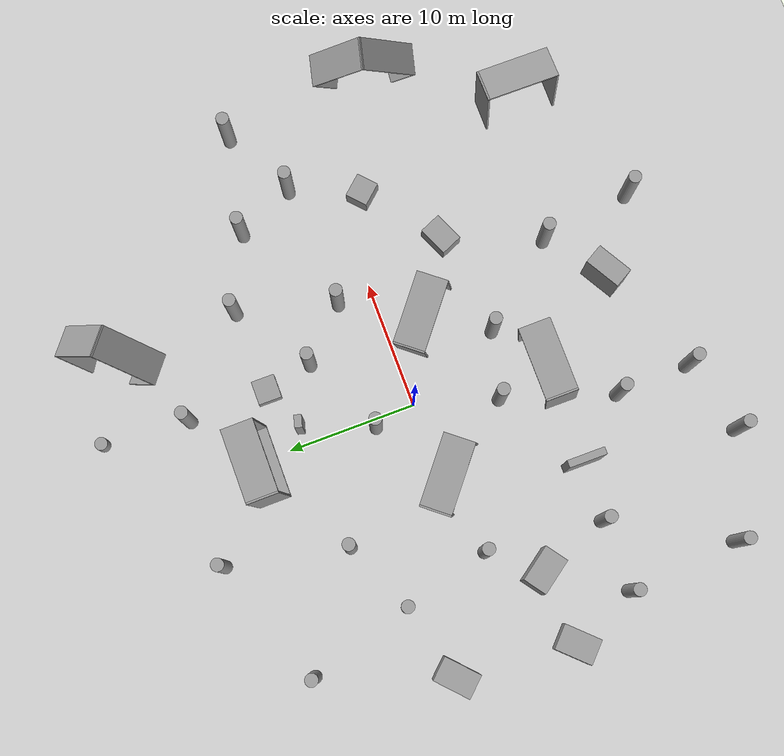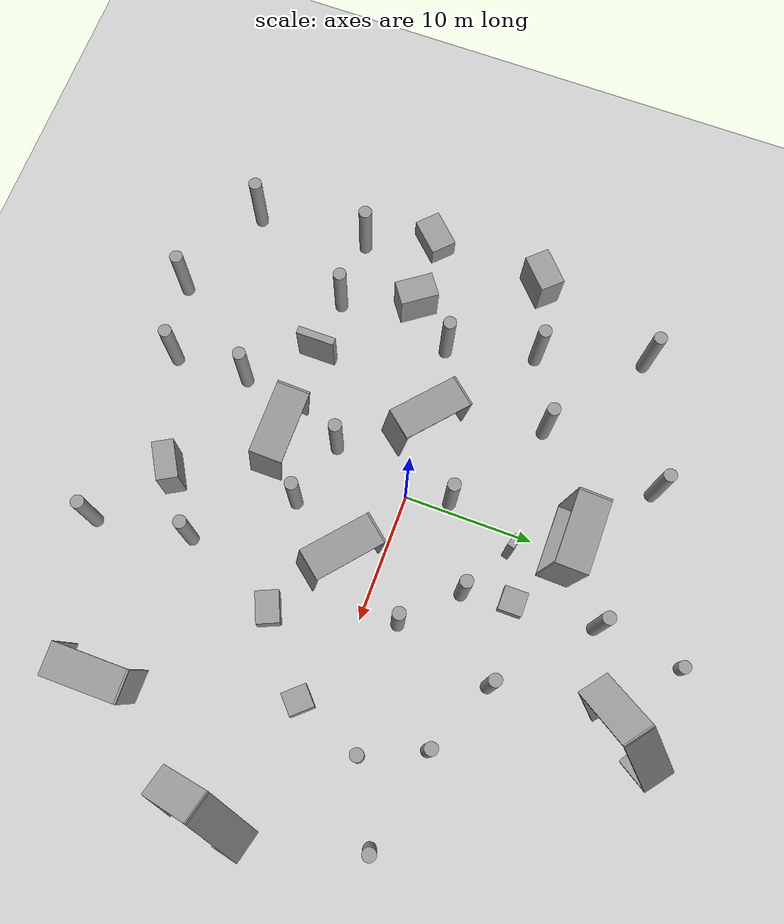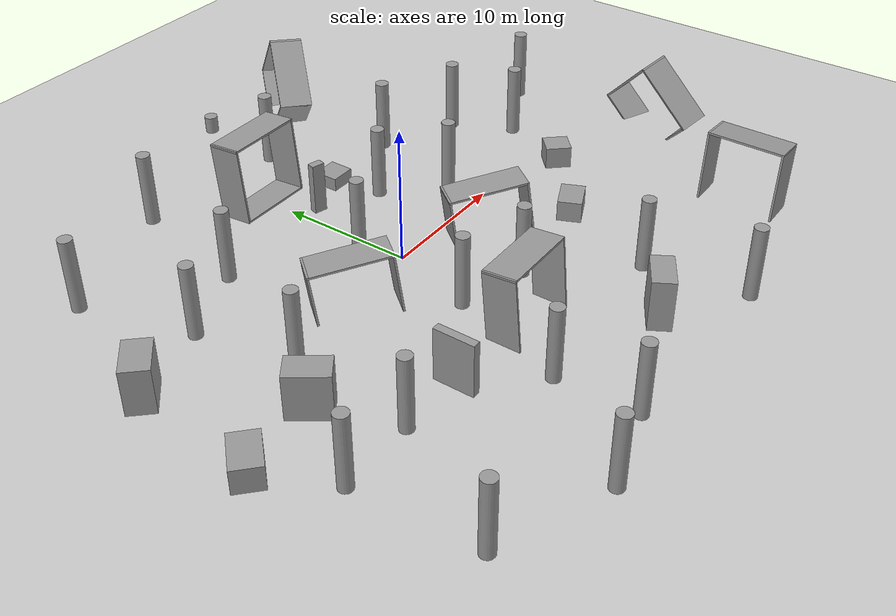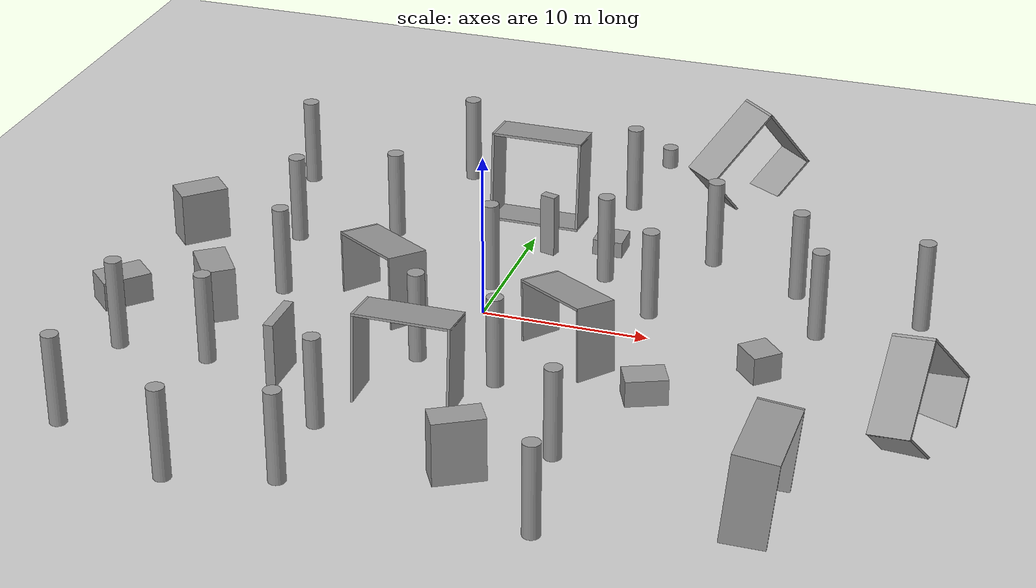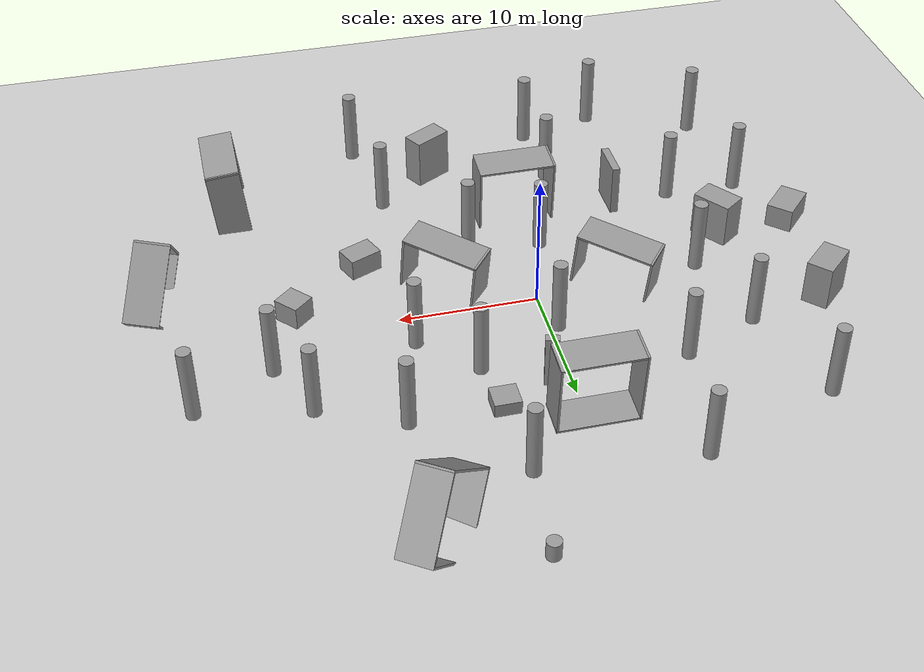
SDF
<sdf version="1.6">
 <world name="default">
  <light name="sun" type="directional">
   <pose>0 0 10 0 -0 0</pose>
   <diffuse>0.8 0.8 0.8 1</diffuse>
   <specular>0.2 0.2 0.2 1</specular>
   <attenuation>
    <range>1000</range>
    <constant>0.9</constant>
    <linear>0.01</linear>
    <quadratic>0.001</quadratic>
   </attenuation>
   <direction>-0.5 0.1 -0.9</direction>
  </light>
  <model name="ground_plane">
   <static>1</static>
   <link name="link">
    <collision name="collision">
     <geometry><plane><normal>0 0 1</normal><size>100 100</size></plane></geometry>
     <surface><friction><ode><mu>100</mu><mu2>50</mu2></ode></friction></surface>
    </collision>
    <visual name="visual">
     <cast_shadows>0</cast_shadows>
     <geometry><plane><normal>0 0 1</normal><size>100 100</size></plane></geometry>
     <material>
      <script><uri>file://media/materials/scripts/gazebo.material</uri><name>Gazebo/Grey</name></script>
     </material>
    </visual>
   </link>
  </model>
  <gravity>0 0 -9.8</gravity>
  <magnetic_field>6e-06 2.3e-05 -4.2e-05</magnetic_field>
  <atmosphere type="adiabatic"/>
  <physics name="default_physics" default="0" type="ode">
   <max_step_size>0.001</max_step_size>
   <real_time_factor>1</real_time_factor>
   <real_time_update_rate>1000</real_time_update_rate>
  </physics>
  <scene><ambient>0.4 0.4 0.4 1</ambient><background>0.7 0.7 0.7 1</background><shadows>1</shadows></scene>
  <audio><device>default</device></audio>
  <spherical_coordinates>
   <surface_model>EARTH_WGS84</surface_model>
   <latitude_deg>0</latitude_deg>
   <longitude_deg>0</longitude_deg>
   <elevation>0</elevation>
   <heading_deg>0</heading_deg>
  </spherical_coordinates>
  <model name="unit_cylinder">
   <pose>5.28034 23.1376 0.661761 0 -0 0.001729</pose>
   <link name="link">
    <inertial>
     <mass>1</mass>
     <inertia><ixx>0.145833</ixx><ixy>0</ixy><ixz>0</ixz><iyy>0.145833</iyy><iyz>0</iyz><izz>0.125</izz></inertia>
    </inertial>
    <collision name="collision">
     <geometry><cylinder><radius>0.5</radius><length>1.32353</length></cylinder></geometry>
    </collision>
    <visual name="visual">
     <geometry><cylinder><radius>0.5</radius><length>1.32353</length></cylinder></geometry>
     <material>
      <script><name>Gazebo/Grey</name><uri>file://media/materials/scripts/gazebo.material</uri></script>
     </material>
    </visual>
   </link>
  </model>
  <model name="unit_cylinder_clone_2">
   <pose>9.34612 2.72453 2.75253 0 -0 0.007033</pose>
   <link name="link">
    <inertial>
     <mass>1</mass>
     <inertia><ixx>0.145833</ixx><ixy>0</ixy><ixz>0</ixz><iyy>0.145833</iyy><iyz>0</iyz><izz>0.125</izz></inertia>
    </inertial>
    <collision name="collision">
     <geometry><cylinder><radius>0.5</radius><length>5.50507</length></cylinder></geometry>
    </collision>
    <visual name="visual">
     <geometry><cylinder><radius>0.5</radius><length>5.50507</length></cylinder></geometry>
     <material>
      <script><name>Gazebo/Grey</name><uri>file://media/materials/scripts/gazebo.material</uri></script>
     </material>
    </visual>
   </link>
  </model>
  <model name="unit_cylinder_clone_4">
   <pose>8.59201 -13.9206 2.75253 0 -0 0.007526</pose>
   <link name="link">
    <inertial>
     <mass>1</mass>
     <inertia><ixx>0.145833</ixx><ixy>0</ixy><ixz>0</ixz><iyy>0.145833</iyy><iyz>0</iyz><izz>0.125</izz></inertia>
    </inertial>
    <collision name="collision">
     <geometry><cylinder><radius>0.5</radius><length>5.50507</length></cylinder></geometry>
    </collision>
    <visual name="visual">
     <geometry><cylinder><radius>0.5</radius><length>5.50507</length></cylinder></geometry>
     <material>
      <script><name>Gazebo/Grey</name><uri>file://media/materials/scripts/gazebo.material</uri></script>
     </material>
    </visual>
   </link>
  </model>
  <model name="unit_cylinder_clone_5">
   <pose>5.63029 6.34759 2.75253 0 -0 0.006959</pose>
   <link name="link">
    <inertial>
     <mass>1</mass>
     <inertia><ixx>0.145833</ixx><ixy>0</ixy><ixz>0</ixz><iyy>0.145833</iyy><iyz>0</iyz><izz>0.125</izz></inertia>
    </inertial>
    <collision name="collision">
     <geometry><cylinder><radius>0.5</radius><length>5.50507</length></cylinder></geometry>
    </collision>
    <visual name="visual">
     <geometry><cylinder><radius>0.5</radius><length>5.50507</length></cylinder></geometry>
     <material>
      <script><name>Gazebo/Grey</name><uri>file://media/materials/scripts/gazebo.material</uri></script>
     </material>
    </visual>
   </link>
  </model>
  <model name="unit_cylinder_clone_8">
   <pose>11.3719 10.3631 2.75253 0 -0 0.007031</pose>
   <link name="link">
    <inertial>
     <mass>1</mass>
     <inertia><ixx>0.145833</ixx><ixy>0</ixy><ixz>0</ixz><iyy>0.145833</iyy><iyz>0</iyz><izz>0.125</izz></inertia>
    </inertial>
    <collision name="collision">
     <geometry><cylinder><radius>0.5</radius><length>5.50507</length></cylinder></geometry>
    </collision>
    <visual name="visual">
     <geometry><cylinder><radius>0.5</radius><length>5.50507</length></cylinder></geometry>
     <material>
      <script><name>Gazebo/Grey</name><uri>file://media/materials/scripts/gazebo.material</uri></script>
     </material>
    </visual>
   </link>
  </model>
  <model name="unit_cylinder_clone_9">
   <pose>-0.632732 3.27501 2.75253 0 -0 0.007234</pose>
   <link name="link">
    <inertial>
     <mass>1</mass>
     <inertia><ixx>0.145833</ixx><ixy>0</ixy><ixz>0</ixz><iyy>0.145833</iyy><iyz>0</iyz><izz>0.125</izz></inertia>
    </inertial>
    <collision name="collision">
     <geometry><cylinder><radius>0.5</radius><length>5.50507</length></cylinder></geometry>
    </collision>
    <visual name="visual">
     <geometry><cylinder><radius>0.5</radius><length>5.50507</length></cylinder></geometry>
     <material>
      <script><name>Gazebo/Grey</name><uri>file://media/materials/scripts/gazebo.material</uri></script>
     </material>
    </visual>
   </link>
  </model>
  <model name="unit_box_clone">
   <pose>11.597 -6.53716 0.788235 0 0 -1.1581</pose>
   <link name="link">
    <inertial>
     <mass>1</mass>
     <inertia>
      <ixx>0.166667</ixx>
      <ixy>0</ixy>
      <ixz>0</ixz>
      <iyy>0.166667</iyy>
      <iyz>0</iyz>
      <izz>0.166667</izz>
     </inertia>
    </inertial>
    <collision name="collision"><geometry><box><size>1.76997 2.44518 1.57647</size></box></geometry></collision>
    <visual name="visual">
     <geometry><box><size>1.76997 2.44518 1.57647</size></box></geometry>
     <material>
      <script><name>Gazebo/Grey</name><uri>file://media/materials/scripts/gazebo.material</uri></script>
     </material>
    </visual>
   </link>
  </model>
  <model name="unit_box_clone_0">
   <pose>17.0391 -2.04264 0.84104 0 -0 0.734782</pose>
   <link name="link">
    <inertial>
     <mass>1</mass>
     <inertia>
      <ixx>0.166667</ixx>
      <ixy>0</ixy>
      <ixz>0</ixz>
      <iyy>0.166667</iyy>
      <iyz>0</iyz>
      <izz>0.166667</izz>
     </inertia>
    </inertial>
    <collision name="collision"><geometry><box><size>1.76997 1.92154 1.68208</size></box></geometry></collision>
    <visual name="visual">
     <geometry><box><size>1.76997 1.92154 1.68208</size></box></geometry>
     <material>
      <script><name>Gazebo/Grey</name><uri>file://media/materials/scripts/gazebo.material</uri></script>
     </material>
    </visual>
   </link>
  </model>
  <model name="unit_cylinder_clone_7_clone_0">
   <pose>24.7832 6.25194 2.75253 0 -0 0.006995</pose>
   <link name="link">
    <inertial>
     <mass>1</mass>
     <inertia><ixx>0.145833</ixx><ixy>0</ixy><ixz>0</ixz><iyy>0.145833</iyy><iyz>0</iyz><izz>0.125</izz></inertia>
    </inertial>
    <collision name="collision">
     <geometry><cylinder><radius>0.5</radius><length>5.50507</length></cylinder></geometry>
    </collision>
    <visual name="visual">
     <geometry><cylinder><radius>0.5</radius><length>5.50507</length></cylinder></geometry>
     <material>
      <script><name>Gazebo/Grey</name><uri>file://media/materials/scripts/gazebo.material</uri></script>
     </material>
    </visual>
   </link>
  </model>
  <model name="unit_cylinder_clone_7_clone_2">
   <pose>-8.46768 8.17615 2.75253 0 -0 0.007287</pose>
   <link name="link">
    <inertial>
     <mass>1</mass>
     <inertia><ixx>0.145833</ixx><ixy>0</ixy><ixz>0</ixz><iyy>0.145833</iyy><iyz>0</iyz><izz>0.125</izz></inertia>
    </inertial>
    <collision name="collision">
     <geometry><cylinder><radius>0.5</radius><length>5.50507</length></cylinder></geometry>
    </collision>
    <visual name="visual">
     <geometry><cylinder><radius>0.5</radius><length>5.50507</length></cylinder></geometry>
     <material>
      <script><name>Gazebo/Grey</name><uri>file://media/materials/scripts/gazebo.material</uri></script>
     </material>
    </visual>
   </link>
  </model>
  <model name="vRoom_clone_3_clone_clone_9">
   <link name="Wall_0">
    <pose>-2.8 -0 -1e-06 -0 -0 -1.5708</pose>
    <velocity_decay><linear>0</linear><angular>0</angular></velocity_decay>
    <visual name="Wall_0_Visual">
     <pose>0 0 1.25 0 -0 0</pose>
     <geometry><box><size>5.75 0.15 2.5</size></box></geometry>
     <material>
      <script><uri>file://media/materials/scripts/gazebo.material</uri><name>Gazebo/Grey</name></script>
      <ambient>1 1 1 1</ambient>
     </material>
    </visual>
    <collision name="Wall_0_Collision">
     <pose>0 0 1.25 0 -0 0</pose>
     <geometry><box><size>5.75 0.15 2.5</size></box></geometry>
     <surface>
      <friction>
       <ode><mu>1</mu><mu2>1</mu2><fdir1>0 0 0</fdir1><slip1>0</slip1><slip2>0</slip2></ode>
       <torsional>
        <coefficient>1</coefficient>
        <patch_radius>0</patch_radius>
        <surface_radius>0</surface_radius>
        <use_patch_radius>1</use_patch_radius>
        <ode><slip>0</slip></ode>
       </torsional>
      </friction>
      <bounce><restitution_coefficient>0</restitution_coefficient><threshold>1e+06</threshold></bounce>
      <contact>
       <collide_without_contact>0</collide_without_contact>
       <collide_without_contact_bitmask>1</collide_without_contact_bitmask>
       <collide_bitmask>1</collide_bitmask>
       <ode>
        <soft_cfm>0</soft_cfm>
        <soft_erp>0.2</soft_erp>
        <kp>1e+13</kp>
        <kd>1</kd>
        <max_vel>0.01</max_vel>
        <min_depth>0</min_depth>
       </ode>
       <bullet>
        <split_impulse>1</split_impulse>
        <split_impulse_penetration_threshold>-0.01</split_impulse_penetration_threshold>
        <soft_cfm>0</soft_cfm>
        <soft_erp>0.2</soft_erp>
        <kp>1e+13</kp>
        <kd>1</kd>
       </bullet>
      </contact>
     </surface>
    </collision>
   </link>
   <link name="Wall_1">
    <pose>2e-06 -2.8 2e-06 0 -0 0</pose>
    <velocity_decay><linear>0</linear><angular>0</angular></velocity_decay>
    <visual name="Wall_1_Visual">
     <pose>0 0 1.25 0 -0 0</pose>
     <geometry><box><size>5.75 0.15 2.5</size></box></geometry>
     <material>
      <script><uri>file://media/materials/scripts/gazebo.material</uri><name>Gazebo/Grey</name></script>
      <ambient>1 1 1 1</ambient>
     </material>
    </visual>
    <collision name="Wall_1_Collision">
     <pose>0 0 1.25 0 -0 0</pose>
     <geometry><box><size>5.75 0.15 2.5</size></box></geometry>
     <surface>
      <friction>
       <ode><mu>1</mu><mu2>1</mu2><fdir1>0 0 0</fdir1><slip1>0</slip1><slip2>0</slip2></ode>
       <torsional>
        <coefficient>1</coefficient>
        <patch_radius>0</patch_radius>
        <surface_radius>0</surface_radius>
        <use_patch_radius>1</use_patch_radius>
        <ode><slip>0</slip></ode>
       </torsional>
      </friction>
      <bounce><restitution_coefficient>0</restitution_coefficient><threshold>1e+06</threshold></bounce>
      <contact>
       <collide_without_contact>0</collide_without_contact>
       <collide_without_contact_bitmask>1</collide_without_contact_bitmask>
       <collide_bitmask>1</collide_bitmask>
       <ode>
        <soft_cfm>0</soft_cfm>
        <soft_erp>0.2</soft_erp>
        <kp>1e+13</kp>
        <kd>1</kd>
        <max_vel>0.01</max_vel>
        <min_depth>0</min_depth>
       </ode>
       <bullet>
        <split_impulse>1</split_impulse>
        <split_impulse_penetration_threshold>-0.01</split_impulse_penetration_threshold>
        <soft_cfm>0</soft_cfm>
        <soft_erp>0.2</soft_erp>
        <kp>1e+13</kp>
        <kd>1</kd>
       </bullet>
      </contact>
     </surface>
    </collision>
   </link>
   <link name="Wall_2">
    <pose>2.8 0 1e-06 0 -0 1.5708</pose>
    <velocity_decay><linear>0</linear><angular>0</angular></velocity_decay>
    <visual name="Wall_2_Visual">
     <pose>0 0 1.25 0 -0 0</pose>
     <geometry><box><size>5.75 0.15 2.5</size></box></geometry>
     <material>
      <script><uri>file://media/materials/scripts/gazebo.material</uri><name>Gazebo/Grey</name></script>
      <ambient>1 1 1 1</ambient>
     </material>
    </visual>
    <collision name="Wall_2_Collision">
     <pose>0 0 1.25 0 -0 0</pose>
     <geometry><box><size>5.75 0.15 2.5</size></box></geometry>
     <surface>
      <friction>
       <ode><mu>1</mu><mu2>1</mu2><fdir1>0 0 0</fdir1><slip1>0</slip1><slip2>0</slip2></ode>
       <torsional>
        <coefficient>1</coefficient>
        <patch_radius>0</patch_radius>
        <surface_radius>0</surface_radius>
        <use_patch_radius>1</use_patch_radius>
        <ode><slip>0</slip></ode>
       </torsional>
      </friction>
      <bounce><restitution_coefficient>0</restitution_coefficient><threshold>1e+06</threshold></bounce>
      <contact>
       <collide_without_contact>0</collide_without_contact>
       <collide_without_contact_bitmask>1</collide_without_contact_bitmask>
       <collide_bitmask>1</collide_bitmask>
       <ode>
        <soft_cfm>0</soft_cfm>
        <soft_erp>0.2</soft_erp>
        <kp>1e+13</kp>
        <kd>1</kd>
        <max_vel>0.01</max_vel>
        <min_depth>0</min_depth>
       </ode>
       <bullet>
        <split_impulse>1</split_impulse>
        <split_impulse_penetration_threshold>-0.01</split_impulse_penetration_threshold>
        <soft_cfm>0</soft_cfm>
        <soft_erp>0.2</soft_erp>
        <kp>1e+13</kp>
        <kd>1</kd>
       </bullet>
      </contact>
     </surface>
    </collision>
   </link>
   <link name="Wall_3">
    <pose>-2e-06 2.8 -2e-06 0 -0 3.14159</pose>
    <velocity_decay><linear>0</linear><angular>0</angular></velocity_decay>
    <visual name="Wall_3_Visual">
     <pose>0 0 1.25 0 -0 0</pose>
     <geometry><box><size>5.75 0.15 2.5</size></box></geometry>
     <material>
      <script><uri>file://media/materials/scripts/gazebo.material</uri><name>Gazebo/Grey</name></script>
      <ambient>1 1 1 1</ambient>
     </material>
    </visual>
    <collision name="Wall_3_Collision">
     <pose>0 0 1.25 0 -0 0</pose>
     <geometry><box><size>5.75 0.15 2.5</size></box></geometry>
     <surface>
      <friction>
       <ode><mu>1</mu><mu2>1</mu2><fdir1>0 0 0</fdir1><slip1>0</slip1><slip2>0</slip2></ode>
       <torsional>
        <coefficient>1</coefficient>
        <patch_radius>0</patch_radius>
        <surface_radius>0</surface_radius>
        <use_patch_radius>1</use_patch_radius>
        <ode><slip>0</slip></ode>
       </torsional>
      </friction>
      <bounce><restitution_coefficient>0</restitution_coefficient><threshold>1e+06</threshold></bounce>
      <contact>
       <collide_without_contact>0</collide_without_contact>
       <collide_without_contact_bitmask>1</collide_without_contact_bitmask>
       <collide_bitmask>1</collide_bitmask>
       <ode>
        <soft_cfm>0</soft_cfm>
        <soft_erp>0.2</soft_erp>
        <kp>1e+13</kp>
        <kd>1</kd>
        <max_vel>0.01</max_vel>
        <min_depth>0</min_depth>
       </ode>
       <bullet>
        <split_impulse>1</split_impulse>
        <split_impulse_penetration_threshold>-0.01</split_impulse_penetration_threshold>
        <soft_cfm>0</soft_cfm>
        <soft_erp>0.2</soft_erp>
        <kp>1e+13</kp>
        <kd>1</kd>
       </bullet>
      </contact>
     </surface>
    </collision>
   </link>
   <static>1</static>
   <pose>21.486 -16.0168 2.16039 4e-06 -1.47998 -7e-06</pose>
  </model>
  <model name="vRoom_clone_3_clone_clone_9_clone_0">
   <link name="Wall_0">
    <pose>-2.8 -0 -1e-06 -0 -0 -1.5708</pose>
    <velocity_decay><linear>0</linear><angular>0</angular></velocity_decay>
    <visual name="Wall_0_Visual">
     <pose>0 0 1.25 0 -0 0</pose>
     <geometry><box><size>5.75 0.15 2.5</size></box></geometry>
     <material>
      <script><uri>file://media/materials/scripts/gazebo.material</uri><name>Gazebo/Grey</name></script>
      <ambient>1 1 1 1</ambient>
     </material>
    </visual>
    <collision name="Wall_0_Collision">
     <pose>0 0 1.25 0 -0 0</pose>
     <geometry><box><size>5.75 0.15 2.5</size></box></geometry>
     <surface>
      <friction>
       <ode><mu>1</mu><mu2>1</mu2><fdir1>0 0 0</fdir1><slip1>0</slip1><slip2>0</slip2></ode>
       <torsional>
        <coefficient>1</coefficient>
        <patch_radius>0</patch_radius>
        <surface_radius>0</surface_radius>
        <use_patch_radius>1</use_patch_radius>
        <ode><slip>0</slip></ode>
       </torsional>
      </friction>
      <bounce><restitution_coefficient>0</restitution_coefficient><threshold>1e+06</threshold></bounce>
      <contact>
       <collide_without_contact>0</collide_without_contact>
       <collide_without_contact_bitmask>1</collide_without_contact_bitmask>
       <collide_bitmask>1</collide_bitmask>
       <ode>
        <soft_cfm>0</soft_cfm>
        <soft_erp>0.2</soft_erp>
        <kp>1e+13</kp>
        <kd>1</kd>
        <max_vel>0.01</max_vel>
        <min_depth>0</min_depth>
       </ode>
       <bullet>
        <split_impulse>1</split_impulse>
        <split_impulse_penetration_threshold>-0.01</split_impulse_penetration_threshold>
        <soft_cfm>0</soft_cfm>
        <soft_erp>0.2</soft_erp>
        <kp>1e+13</kp>
        <kd>1</kd>
       </bullet>
      </contact>
     </surface>
    </collision>
   </link>
   <link name="Wall_1">
    <pose>2e-06 -2.8 2e-06 0 -0 0</pose>
    <velocity_decay><linear>0</linear><angular>0</angular></velocity_decay>
    <visual name="Wall_1_Visual">
     <pose>0 0 1.25 0 -0 0</pose>
     <geometry><box><size>5.75 0.15 2.5</size></box></geometry>
     <material>
      <script><uri>file://media/materials/scripts/gazebo.material</uri><name>Gazebo/Grey</name></script>
      <ambient>1 1 1 1</ambient>
     </material>
    </visual>
    <collision name="Wall_1_Collision">
     <pose>0 0 1.25 0 -0 0</pose>
     <geometry><box><size>5.75 0.15 2.5</size></box></geometry>
     <surface>
      <friction>
       <ode><mu>1</mu><mu2>1</mu2><fdir1>0 0 0</fdir1><slip1>0</slip1><slip2>0</slip2></ode>
       <torsional>
        <coefficient>1</coefficient>
        <patch_radius>0</patch_radius>
        <surface_radius>0</surface_radius>
        <use_patch_radius>1</use_patch_radius>
        <ode><slip>0</slip></ode>
       </torsional>
      </friction>
      <bounce><restitution_coefficient>0</restitution_coefficient><threshold>1e+06</threshold></bounce>
      <contact>
       <collide_without_contact>0</collide_without_contact>
       <collide_without_contact_bitmask>1</collide_without_contact_bitmask>
       <collide_bitmask>1</collide_bitmask>
       <ode>
        <soft_cfm>0</soft_cfm>
        <soft_erp>0.2</soft_erp>
        <kp>1e+13</kp>
        <kd>1</kd>
        <max_vel>0.01</max_vel>
        <min_depth>0</min_depth>
       </ode>
       <bullet>
        <split_impulse>1</split_impulse>
        <split_impulse_penetration_threshold>-0.01</split_impulse_penetration_threshold>
        <soft_cfm>0</soft_cfm>
        <soft_erp>0.2</soft_erp>
        <kp>1e+13</kp>
        <kd>1</kd>
       </bullet>
      </contact>
     </surface>
    </collision>
   </link>
   <link name="Wall_2">
    <pose>2.8 0 1e-06 0 -0 1.5708</pose>
    <velocity_decay><linear>0</linear><angular>0</angular></velocity_decay>
    <visual name="Wall_2_Visual">
     <pose>0 0 1.25 0 -0 0</pose>
     <geometry><box><size>5.75 0.15 2.5</size></box></geometry>
     <material>
      <script><uri>file://media/materials/scripts/gazebo.material</uri><name>Gazebo/Grey</name></script>
      <ambient>1 1 1 1</ambient>
     </material>
    </visual>
    <collision name="Wall_2_Collision">
     <pose>0 0 1.25 0 -0 0</pose>
     <geometry><box><size>5.75 0.15 2.5</size></box></geometry>
     <surface>
      <friction>
       <ode><mu>1</mu><mu2>1</mu2><fdir1>0 0 0</fdir1><slip1>0</slip1><slip2>0</slip2></ode>
       <torsional>
        <coefficient>1</coefficient>
        <patch_radius>0</patch_radius>
        <surface_radius>0</surface_radius>
        <use_patch_radius>1</use_patch_radius>
        <ode><slip>0</slip></ode>
       </torsional>
      </friction>
      <bounce><restitution_coefficient>0</restitution_coefficient><threshold>1e+06</threshold></bounce>
      <contact>
       <collide_without_contact>0</collide_without_contact>
       <collide_without_contact_bitmask>1</collide_without_contact_bitmask>
       <collide_bitmask>1</collide_bitmask>
       <ode>
        <soft_cfm>0</soft_cfm>
        <soft_erp>0.2</soft_erp>
        <kp>1e+13</kp>
        <kd>1</kd>
        <max_vel>0.01</max_vel>
        <min_depth>0</min_depth>
       </ode>
       <bullet>
        <split_impulse>1</split_impulse>
        <split_impulse_penetration_threshold>-0.01</split_impulse_penetration_threshold>
        <soft_cfm>0</soft_cfm>
        <soft_erp>0.2</soft_erp>
        <kp>1e+13</kp>
        <kd>1</kd>
       </bullet>
      </contact>
     </surface>
    </collision>
   </link>
   <link name="Wall_3">
    <pose>-2e-06 2.8 -2e-06 0 -0 3.14159</pose>
    <velocity_decay><linear>0</linear><angular>0</angular></velocity_decay>
    <visual name="Wall_3_Visual">
     <pose>0 0 1.25 0 -0 0</pose>
     <geometry><box><size>5.75 0.15 2.5</size></box></geometry>
     <material>
      <script><uri>file://media/materials/scripts/gazebo.material</uri><name>Gazebo/Grey</name></script>
      <ambient>1 1 1 1</ambient>
     </material>
    </visual>
    <collision name="Wall_3_Collision">
     <pose>0 0 1.25 0 -0 0</pose>
     <geometry><box><size>5.75 0.15 2.5</size></box></geometry>
     <surface>
      <friction>
       <ode><mu>1</mu><mu2>1</mu2><fdir1>0 0 0</fdir1><slip1>0</slip1><slip2>0</slip2></ode>
       <torsional>
        <coefficient>1</coefficient>
        <patch_radius>0</patch_radius>
        <surface_radius>0</surface_radius>
        <use_patch_radius>1</use_patch_radius>
        <ode><slip>0</slip></ode>
       </torsional>
      </friction>
      <bounce><restitution_coefficient>0</restitution_coefficient><threshold>1e+06</threshold></bounce>
      <contact>
       <collide_without_contact>0</collide_without_contact>
       <collide_without_contact_bitmask>1</collide_without_contact_bitmask>
       <collide_bitmask>1</collide_bitmask>
       <ode>
        <soft_cfm>0</soft_cfm>
        <soft_erp>0.2</soft_erp>
        <kp>1e+13</kp>
        <kd>1</kd>
        <max_vel>0.01</max_vel>
        <min_depth>0</min_depth>
       </ode>
       <bullet>
        <split_impulse>1</split_impulse>
        <split_impulse_penetration_threshold>-0.01</split_impulse_penetration_threshold>
        <soft_cfm>0</soft_cfm>
        <soft_erp>0.2</soft_erp>
        <kp>1e+13</kp>
        <kd>1</kd>
       </bullet>
      </contact>
     </surface>
    </collision>
   </link>
   <static>1</static>
   <pose>6.88312 -2.08616 1 -1.11103 -1.4406 1.99896</pose>
  </model>
  <model name="vRoom_clone_3_clone_clone_9_clone_1">
   <link name="Wall_0">
    <pose>-2.8 -0 -1e-06 -0 -0 -1.5708</pose>
    <velocity_decay><linear>0</linear><angular>0</angular></velocity_decay>
    <visual name="Wall_0_Visual">
     <pose>0 0 1.25 0 -0 0</pose>
     <geometry><box><size>5.75 0.15 2.5</size></box></geometry>
     <material>
      <script><uri>file://media/materials/scripts/gazebo.material</uri><name>Gazebo/Grey</name></script>
      <ambient>1 1 1 1</ambient>
     </material>
    </visual>
    <collision name="Wall_0_Collision">
     <pose>0 0 1.25 0 -0 0</pose>
     <geometry><box><size>5.75 0.15 2.5</size></box></geometry>
     <surface>
      <friction>
       <ode><mu>1</mu><mu2>1</mu2><fdir1>0 0 0</fdir1><slip1>0</slip1><slip2>0</slip2></ode>
       <torsional>
        <coefficient>1</coefficient>
        <patch_radius>0</patch_radius>
        <surface_radius>0</surface_radius>
        <use_patch_radius>1</use_patch_radius>
        <ode><slip>0</slip></ode>
       </torsional>
      </friction>
      <bounce><restitution_coefficient>0</restitution_coefficient><threshold>1e+06</threshold></bounce>
      <contact>
       <collide_without_contact>0</collide_without_contact>
       <collide_without_contact_bitmask>1</collide_without_contact_bitmask>
       <collide_bitmask>1</collide_bitmask>
       <ode>
        <soft_cfm>0</soft_cfm>
        <soft_erp>0.2</soft_erp>
        <kp>1e+13</kp>
        <kd>1</kd>
        <max_vel>0.01</max_vel>
        <min_depth>0</min_depth>
       </ode>
       <bullet>
        <split_impulse>1</split_impulse>
        <split_impulse_penetration_threshold>-0.01</split_impulse_penetration_threshold>
        <soft_cfm>0</soft_cfm>
        <soft_erp>0.2</soft_erp>
        <kp>1e+13</kp>
        <kd>1</kd>
       </bullet>
      </contact>
     </surface>
    </collision>
   </link>
   <link name="Wall_1">
    <pose>2e-06 -2.8 2e-06 0 -0 0</pose>
    <velocity_decay><linear>0</linear><angular>0</angular></velocity_decay>
    <visual name="Wall_1_Visual">
     <pose>0 0 1.25 0 -0 0</pose>
     <geometry><box><size>5.75 0.15 2.5</size></box></geometry>
     <material>
      <script><uri>file://media/materials/scripts/gazebo.material</uri><name>Gazebo/Grey</name></script>
      <ambient>1 1 1 1</ambient>
     </material>
    </visual>
    <collision name="Wall_1_Collision">
     <pose>0 0 1.25 0 -0 0</pose>
     <geometry><box><size>5.75 0.15 2.5</size></box></geometry>
     <surface>
      <friction>
       <ode><mu>1</mu><mu2>1</mu2><fdir1>0 0 0</fdir1><slip1>0</slip1><slip2>0</slip2></ode>
       <torsional>
        <coefficient>1</coefficient>
        <patch_radius>0</patch_radius>
        <surface_radius>0</surface_radius>
        <use_patch_radius>1</use_patch_radius>
        <ode><slip>0</slip></ode>
       </torsional>
      </friction>
      <bounce><restitution_coefficient>0</restitution_coefficient><threshold>1e+06</threshold></bounce>
      <contact>
       <collide_without_contact>0</collide_without_contact>
       <collide_without_contact_bitmask>1</collide_without_contact_bitmask>
       <collide_bitmask>1</collide_bitmask>
       <ode>
        <soft_cfm>0</soft_cfm>
        <soft_erp>0.2</soft_erp>
        <kp>1e+13</kp>
        <kd>1</kd>
        <max_vel>0.01</max_vel>
        <min_depth>0</min_depth>
       </ode>
       <bullet>
        <split_impulse>1</split_impulse>
        <split_impulse_penetration_threshold>-0.01</split_impulse_penetration_threshold>
        <soft_cfm>0</soft_cfm>
        <soft_erp>0.2</soft_erp>
        <kp>1e+13</kp>
        <kd>1</kd>
       </bullet>
      </contact>
     </surface>
    </collision>
   </link>
   <link name="Wall_2">
    <pose>2.8 0 1e-06 0 -0 1.5708</pose>
    <velocity_decay><linear>0</linear><angular>0</angular></velocity_decay>
    <visual name="Wall_2_Visual">
     <pose>0 0 1.25 0 -0 0</pose>
     <geometry><box><size>5.75 0.15 2.5</size></box></geometry>
     <material>
      <script><uri>file://media/materials/scripts/gazebo.material</uri><name>Gazebo/Grey</name></script>
      <ambient>1 1 1 1</ambient>
     </material>
    </visual>
    <collision name="Wall_2_Collision">
     <pose>0 0 1.25 0 -0 0</pose>
     <geometry><box><size>5.75 0.15 2.5</size></box></geometry>
     <surface>
      <friction>
       <ode><mu>1</mu><mu2>1</mu2><fdir1>0 0 0</fdir1><slip1>0</slip1><slip2>0</slip2></ode>
       <torsional>
        <coefficient>1</coefficient>
        <patch_radius>0</patch_radius>
        <surface_radius>0</surface_radius>
        <use_patch_radius>1</use_patch_radius>
        <ode><slip>0</slip></ode>
       </torsional>
      </friction>
      <bounce><restitution_coefficient>0</restitution_coefficient><threshold>1e+06</threshold></bounce>
      <contact>
       <collide_without_contact>0</collide_without_contact>
       <collide_without_contact_bitmask>1</collide_without_contact_bitmask>
       <collide_bitmask>1</collide_bitmask>
       <ode>
        <soft_cfm>0</soft_cfm>
        <soft_erp>0.2</soft_erp>
        <kp>1e+13</kp>
        <kd>1</kd>
        <max_vel>0.01</max_vel>
        <min_depth>0</min_depth>
       </ode>
       <bullet>
        <split_impulse>1</split_impulse>
        <split_impulse_penetration_threshold>-0.01</split_impulse_penetration_threshold>
        <soft_cfm>0</soft_cfm>
        <soft_erp>0.2</soft_erp>
        <kp>1e+13</kp>
        <kd>1</kd>
       </bullet>
      </contact>
     </surface>
    </collision>
   </link>
   <link name="Wall_3">
    <pose>-2e-06 2.8 -2e-06 0 -0 3.14159</pose>
    <velocity_decay><linear>0</linear><angular>0</angular></velocity_decay>
    <visual name="Wall_3_Visual">
     <pose>0 0 1.25 0 -0 0</pose>
     <geometry><box><size>5.75 0.15 2.5</size></box></geometry>
     <material>
      <script><uri>file://media/materials/scripts/gazebo.material</uri><name>Gazebo/Grey</name></script>
      <ambient>1 1 1 1</ambient>
     </material>
    </visual>
    <collision name="Wall_3_Collision">
     <pose>0 0 1.25 0 -0 0</pose>
     <geometry><box><size>5.75 0.15 2.5</size></box></geometry>
     <surface>
      <friction>
       <ode><mu>1</mu><mu2>1</mu2><fdir1>0 0 0</fdir1><slip1>0</slip1><slip2>0</slip2></ode>
       <torsional>
        <coefficient>1</coefficient>
        <patch_radius>0</patch_radius>
        <surface_radius>0</surface_radius>
        <use_patch_radius>1</use_patch_radius>
        <ode><slip>0</slip></ode>
       </torsional>
      </friction>
      <bounce><restitution_coefficient>0</restitution_coefficient><threshold>1e+06</threshold></bounce>
      <contact>
       <collide_without_contact>0</collide_without_contact>
       <collide_without_contact_bitmask>1</collide_without_contact_bitmask>
       <collide_bitmask>1</collide_bitmask>
       <ode>
        <soft_cfm>0</soft_cfm>
        <soft_erp>0.2</soft_erp>
        <kp>1e+13</kp>
        <kd>1</kd>
        <max_vel>0.01</max_vel>
        <min_depth>0</min_depth>
       </ode>
       <bullet>
        <split_impulse>1</split_impulse>
        <split_impulse_penetration_threshold>-0.01</split_impulse_penetration_threshold>
        <soft_cfm>0</soft_cfm>
        <soft_erp>0.2</soft_erp>
        <kp>1e+13</kp>
        <kd>1</kd>
       </bullet>
      </contact>
     </surface>
    </collision>
   </link>
   <static>1</static>
   <pose>-0.451678 13.821 3.0326 4e-06 -1.47998 1.57</pose>
  </model>
  <model name="vRoom_clone_3_clone_clone_9_clone_2">
   <link name="Wall_0">
    <pose>-2.8 -0 -1e-06 -0 -0 -1.5708</pose>
    <velocity_decay><linear>0</linear><angular>0</angular></velocity_decay>
    <visual name="Wall_0_Visual">
     <pose>0 0 1.25 0 -0 0</pose>
     <geometry><box><size>5.75 0.15 2.5</size></box></geometry>
     <material>
      <script><uri>file://media/materials/scripts/gazebo.material</uri><name>Gazebo/Grey</name></script>
      <ambient>1 1 1 1</ambient>
     </material>
    </visual>
    <collision name="Wall_0_Collision">
     <pose>0 0 1.25 0 -0 0</pose>
     <geometry><box><size>5.75 0.15 2.5</size></box></geometry>
     <surface>
      <friction>
       <ode><mu>1</mu><mu2>1</mu2><fdir1>0 0 0</fdir1><slip1>0</slip1><slip2>0</slip2></ode>
       <torsional>
        <coefficient>1</coefficient>
        <patch_radius>0</patch_radius>
        <surface_radius>0</surface_radius>
        <use_patch_radius>1</use_patch_radius>
        <ode><slip>0</slip></ode>
       </torsional>
      </friction>
      <bounce><restitution_coefficient>0</restitution_coefficient><threshold>1e+06</threshold></bounce>
      <contact>
       <collide_without_contact>0</collide_without_contact>
       <collide_without_contact_bitmask>1</collide_without_contact_bitmask>
       <collide_bitmask>1</collide_bitmask>
       <ode>
        <soft_cfm>0</soft_cfm>
        <soft_erp>0.2</soft_erp>
        <kp>1e+13</kp>
        <kd>1</kd>
        <max_vel>0.01</max_vel>
        <min_depth>0</min_depth>
       </ode>
       <bullet>
        <split_impulse>1</split_impulse>
        <split_impulse_penetration_threshold>-0.01</split_impulse_penetration_threshold>
        <soft_cfm>0</soft_cfm>
        <soft_erp>0.2</soft_erp>
        <kp>1e+13</kp>
        <kd>1</kd>
       </bullet>
      </contact>
     </surface>
    </collision>
   </link>
   <link name="Wall_1">
    <pose>2e-06 -2.8 2e-06 0 -0 0</pose>
    <velocity_decay><linear>0</linear><angular>0</angular></velocity_decay>
    <visual name="Wall_1_Visual">
     <pose>0 0 1.25 0 -0 0</pose>
     <geometry><box><size>5.75 0.15 2.5</size></box></geometry>
     <material>
      <script><uri>file://media/materials/scripts/gazebo.material</uri><name>Gazebo/Grey</name></script>
      <ambient>1 1 1 1</ambient>
     </material>
    </visual>
    <collision name="Wall_1_Collision">
     <pose>0 0 1.25 0 -0 0</pose>
     <geometry><box><size>5.75 0.15 2.5</size></box></geometry>
     <surface>
      <friction>
       <ode><mu>1</mu><mu2>1</mu2><fdir1>0 0 0</fdir1><slip1>0</slip1><slip2>0</slip2></ode>
       <torsional>
        <coefficient>1</coefficient>
        <patch_radius>0</patch_radius>
        <surface_radius>0</surface_radius>
        <use_patch_radius>1</use_patch_radius>
        <ode><slip>0</slip></ode>
       </torsional>
      </friction>
      <bounce><restitution_coefficient>0</restitution_coefficient><threshold>1e+06</threshold></bounce>
      <contact>
       <collide_without_contact>0</collide_without_contact>
       <collide_without_contact_bitmask>1</collide_without_contact_bitmask>
       <collide_bitmask>1</collide_bitmask>
       <ode>
        <soft_cfm>0</soft_cfm>
        <soft_erp>0.2</soft_erp>
        <kp>1e+13</kp>
        <kd>1</kd>
        <max_vel>0.01</max_vel>
        <min_depth>0</min_depth>
       </ode>
       <bullet>
        <split_impulse>1</split_impulse>
        <split_impulse_penetration_threshold>-0.01</split_impulse_penetration_threshold>
        <soft_cfm>0</soft_cfm>
        <soft_erp>0.2</soft_erp>
        <kp>1e+13</kp>
        <kd>1</kd>
       </bullet>
      </contact>
     </surface>
    </collision>
   </link>
   <link name="Wall_2">
    <pose>2.8 0 1e-06 0 -0 1.5708</pose>
    <velocity_decay><linear>0</linear><angular>0</angular></velocity_decay>
    <visual name="Wall_2_Visual">
     <pose>0 0 1.25 0 -0 0</pose>
     <geometry><box><size>5.75 0.15 2.5</size></box></geometry>
     <material>
      <script><uri>file://media/materials/scripts/gazebo.material</uri><name>Gazebo/Grey</name></script>
      <ambient>1 1 1 1</ambient>
     </material>
    </visual>
    <collision name="Wall_2_Collision">
     <pose>0 0 1.25 0 -0 0</pose>
     <geometry><box><size>5.75 0.15 2.5</size></box></geometry>
     <surface>
      <friction>
       <ode><mu>1</mu><mu2>1</mu2><fdir1>0 0 0</fdir1><slip1>0</slip1><slip2>0</slip2></ode>
       <torsional>
        <coefficient>1</coefficient>
        <patch_radius>0</patch_radius>
        <surface_radius>0</surface_radius>
        <use_patch_radius>1</use_patch_radius>
        <ode><slip>0</slip></ode>
       </torsional>
      </friction>
      <bounce><restitution_coefficient>0</restitution_coefficient><threshold>1e+06</threshold></bounce>
      <contact>
       <collide_without_contact>0</collide_without_contact>
       <collide_without_contact_bitmask>1</collide_without_contact_bitmask>
       <collide_bitmask>1</collide_bitmask>
       <ode>
        <soft_cfm>0</soft_cfm>
        <soft_erp>0.2</soft_erp>
        <kp>1e+13</kp>
        <kd>1</kd>
        <max_vel>0.01</max_vel>
        <min_depth>0</min_depth>
       </ode>
       <bullet>
        <split_impulse>1</split_impulse>
        <split_impulse_penetration_threshold>-0.01</split_impulse_penetration_threshold>
        <soft_cfm>0</soft_cfm>
        <soft_erp>0.2</soft_erp>
        <kp>1e+13</kp>
        <kd>1</kd>
       </bullet>
      </contact>
     </surface>
    </collision>
   </link>
   <link name="Wall_3">
    <pose>-2e-06 2.8 -2e-06 0 -0 3.14159</pose>
    <velocity_decay><linear>0</linear><angular>0</angular></velocity_decay>
    <visual name="Wall_3_Visual">
     <pose>0 0 1.25 0 -0 0</pose>
     <geometry><box><size>5.75 0.15 2.5</size></box></geometry>
     <material>
      <script><uri>file://media/materials/scripts/gazebo.material</uri><name>Gazebo/Grey</name></script>
      <ambient>1 1 1 1</ambient>
     </material>
    </visual>
    <collision name="Wall_3_Collision">
     <pose>0 0 1.25 0 -0 0</pose>
     <geometry><box><size>5.75 0.15 2.5</size></box></geometry>
     <surface>
      <friction>
       <ode><mu>1</mu><mu2>1</mu2><fdir1>0 0 0</fdir1><slip1>0</slip1><slip2>0</slip2></ode>
       <torsional>
        <coefficient>1</coefficient>
        <patch_radius>0</patch_radius>
        <surface_radius>0</surface_radius>
        <use_patch_radius>1</use_patch_radius>
        <ode><slip>0</slip></ode>
       </torsional>
      </friction>
      <bounce><restitution_coefficient>0</restitution_coefficient><threshold>1e+06</threshold></bounce>
      <contact>
       <collide_without_contact>0</collide_without_contact>
       <collide_without_contact_bitmask>1</collide_without_contact_bitmask>
       <collide_bitmask>1</collide_bitmask>
       <ode>
        <soft_cfm>0</soft_cfm>
        <soft_erp>0.2</soft_erp>
        <kp>1e+13</kp>
        <kd>1</kd>
        <max_vel>0.01</max_vel>
        <min_depth>0</min_depth>
       </ode>
       <bullet>
        <split_impulse>1</split_impulse>
        <split_impulse_penetration_threshold>-0.01</split_impulse_penetration_threshold>
        <soft_cfm>0</soft_cfm>
        <soft_erp>0.2</soft_erp>
        <kp>1e+13</kp>
        <kd>1</kd>
       </bullet>
      </contact>
     </surface>
    </collision>
   </link>
   <static>1</static>
   <pose>27.7206 -5.8322 2 1.8013 -0.792216 -1.97465</pose>
  </model>
  <model name="unit_box_1_clone_0">
   <pose>4.92425 10.1233 0.499994 7e-06 -0 0</pose>
   <link name="link">
    <inertial>
     <mass>1</mass>
     <inertia>
      <ixx>0.166667</ixx>
      <ixy>0</ixy>
      <ixz>0</ixz>
      <iyy>0.166667</iyy>
      <iyz>0</iyz>
      <izz>0.166667</izz>
     </inertia>
    </inertial>
    <collision name="collision"><geometry><box><size>1.86589 1.81745 1</size></box></geometry></collision>
    <visual name="visual">
     <geometry><box><size>1.86589 1.81745 1</size></box></geometry>
     <material>
      <script><name>Gazebo/Grey</name><uri>file://media/materials/scripts/gazebo.material</uri></script>
     </material>
    </visual>
   </link>
  </model>
  <model name="unit_cylinder_clone_9_clone_0">
   <pose>-18.6335 -10.1401 2.75253 0 -0 0.00813</pose>
   <link name="link">
    <inertial>
     <mass>1</mass>
     <inertia><ixx>0.145833</ixx><ixy>0</ixy><ixz>0</ixz><iyy>0.145833</iyy><iyz>0</iyz><izz>0.125</izz></inertia>
    </inertial>
    <collision name="collision">
     <geometry><cylinder><radius>0.5</radius><length>5.50507</length></cylinder></geometry>
    </collision>
    <visual name="visual">
     <geometry><cylinder><radius>0.5</radius><length>5.50507</length></cylinder></geometry>
     <material>
      <script><name>Gazebo/Grey</name><uri>file://media/materials/scripts/gazebo.material</uri></script>
     </material>
    </visual>
   </link>
  </model>
  <model name="unit_cylinder_clone_9_clone_1">
   <pose>-10.2069 -22.173 2.75253 0 -0 0.009019</pose>
   <link name="link">
    <inertial>
     <mass>1</mass>
     <inertia><ixx>0.145833</ixx><ixy>0</ixy><ixz>0</ixz><iyy>0.145833</iyy><iyz>0</iyz><izz>0.125</izz></inertia>
    </inertial>
    <collision name="collision">
     <geometry><cylinder><radius>0.5</radius><length>5.50507</length></cylinder></geometry>
    </collision>
    <visual name="visual">
     <geometry><cylinder><radius>0.5</radius><length>5.50507</length></cylinder></geometry>
     <material>
      <script><name>Gazebo/Grey</name><uri>file://media/materials/scripts/gazebo.material</uri></script>
     </material>
    </visual>
   </link>
  </model>
  <model name="unit_cylinder_clone_9_clone_2">
   <pose>17.1067 7.80346 2.75253 0 -0 0.009123</pose>
   <link name="link">
    <inertial>
     <mass>1</mass>
     <inertia><ixx>0.145833</ixx><ixy>0</ixy><ixz>0</ixz><iyy>0.145833</iyy><iyz>0</iyz><izz>0.125</izz></inertia>
    </inertial>
    <collision name="collision">
     <geometry><cylinder><radius>0.5</radius><length>5.50507</length></cylinder></geometry>
    </collision>
    <visual name="visual">
     <geometry><cylinder><radius>0.5</radius><length>5.50507</length></cylinder></geometry>
     <material>
      <script><name>Gazebo/Grey</name><uri>file://media/materials/scripts/gazebo.material</uri></script>
     </material>
    </visual>
   </link>
  </model>
  <model name="unit_cylinder_clone_9_clone_3">
   <pose>-1.84186 -6.24007 2.75253 0 -0 0.008595</pose>
   <link name="link">
    <inertial>
     <mass>1</mass>
     <inertia><ixx>0.145833</ixx><ixy>0</ixy><ixz>0</ixz><iyy>0.145833</iyy><iyz>0</iyz><izz>0.125</izz></inertia>
    </inertial>
    <collision name="collision">
     <geometry><cylinder><radius>0.5</radius><length>5.50507</length></cylinder></geometry>
    </collision>
    <visual name="visual">
     <geometry><cylinder><radius>0.5</radius><length>5.50507</length></cylinder></geometry>
     <material>
      <script><name>Gazebo/Grey</name><uri>file://media/materials/scripts/gazebo.material</uri></script>
     </material>
    </visual>
   </link>
  </model>
  <model name="unit_cylinder_clone_9_clone_5">
   <pose>-14.0461 5.72199 2.75253 0 -0 0.00823</pose>
   <link name="link">
    <inertial>
     <mass>1</mass>
     <inertia><ixx>0.145833</ixx><ixy>0</ixy><ixz>0</ixz><iyy>0.145833</iyy><iyz>0</iyz><izz>0.125</izz></inertia>
    </inertial>
    <collision name="collision">
     <geometry><cylinder><radius>0.5</radius><length>5.50507</length></cylinder></geometry>
    </collision>
    <visual name="visual">
     <geometry><cylinder><radius>0.5</radius><length>5.50507</length></cylinder></geometry>
     <material>
      <script><name>Gazebo/Grey</name><uri>file://media/materials/scripts/gazebo.material</uri></script>
     </material>
    </visual>
   </link>
  </model>
  <model name="unit_box_2">
   <pose>-8.48938 -10.3568 1.95434 -1e-06 -0 -0.000585</pose>
   <link name="link">
    <inertial>
     <mass>1</mass>
     <inertia>
      <ixx>0.166667</ixx>
      <ixy>0</ixy>
      <ixz>0</ixz>
      <iyy>0.166667</iyy>
      <iyz>0</iyz>
      <izz>0.166667</izz>
     </inertia>
    </inertial>
    <collision name="collision"><geometry><box><size>0.580075 2.95919 3.90868</size></box></geometry></collision>
    <visual name="visual">
     <geometry><box><size>0.580075 2.95919 3.90868</size></box></geometry>
     <material>
      <script><name>Gazebo/Grey</name><uri>file://media/materials/scripts/gazebo.material</uri></script>
     </material>
    </visual>
   </link>
  </model>
  <model name="unit_box_2_clone">
   <pose>4.37377 -17.237 1.88991 -1e-06 -0 -1.04764</pose>
   <link name="link">
    <inertial>
     <mass>1</mass>
     <inertia>
      <ixx>0.166667</ixx>
      <ixy>0</ixy>
      <ixz>0</ixz>
      <iyy>0.166667</iyy>
      <iyz>0</iyz>
      <izz>0.166667</izz>
     </inertia>
    </inertial>
    <collision name="collision"><geometry><box><size>1.62301 2.95919 3.77983</size></box></geometry></collision>
    <visual name="visual">
     <geometry><box><size>1.62301 2.95919 3.77983</size></box></geometry>
     <material>
      <script><name>Gazebo/Grey</name><uri>file://media/materials/scripts/gazebo.material</uri></script>
     </material>
    </visual>
   </link>
  </model>
  <model name="unit_box_2_clone_0">
   <pose>-20.9023 -5.04265 0.899376 1.62226 -1.57079 -2.38505</pose>
   <link name="link">
    <inertial>
     <mass>1</mass>
     <inertia>
      <ixx>0.166667</ixx>
      <ixy>0</ixy>
      <ixz>0</ixz>
      <iyy>0.166667</iyy>
      <iyz>0</iyz>
      <izz>0.166667</izz>
     </inertia>
    </inertial>
    <collision name="collision"><geometry><box><size>1.79876 2.95919 2.00566</size></box></geometry></collision>
    <visual name="visual">
     <geometry><box><size>1.79876 2.95919 2.00566</size></box></geometry>
     <material>
      <script><name>Gazebo/Grey</name><uri>file://media/materials/scripts/gazebo.material</uri></script>
     </material>
    </visual>
   </link>
  </model>
  <model name="unit_box_2_clone_1">
   <pose>-15.0529 -4.60285 1.66336 1e-06 -0 0.625572</pose>
   <link name="link">
    <inertial>
     <mass>1</mass>
     <inertia>
      <ixx>0.166667</ixx>
      <ixy>0</ixy>
      <ixz>0</ixz>
      <iyy>0.166667</iyy>
      <iyz>0</iyz>
      <izz>0.166667</izz>
     </inertia>
    </inertial>
    <collision name="collision"><geometry><box><size>1.91266 2.95919 3.32673</size></box></geometry></collision>
    <visual name="visual">
     <geometry><box><size>1.91266 2.95919 3.32673</size></box></geometry>
     <material>
      <script><name>Gazebo/Grey</name><uri>file://media/materials/scripts/gazebo.material</uri></script>
     </material>
    </visual>
   </link>
  </model>
  <model name="unit_cylinder_clone_9_clone_5_clone">
   <pose>-12.2443 -1.09449 2.75253 0 -0 0.00815</pose>
   <link name="link">
    <inertial>
     <mass>1</mass>
     <inertia><ixx>0.145833</ixx><ixy>0</ixy><ixz>0</ixz><iyy>0.145833</iyy><iyz>0</iyz><izz>0.125</izz></inertia>
    </inertial>
    <collision name="collision">
     <geometry><cylinder><radius>0.5</radius><length>5.50507</length></cylinder></geometry>
    </collision>
    <visual name="visual">
     <geometry><cylinder><radius>0.5</radius><length>5.50507</length></cylinder></geometry>
     <material>
      <script><name>Gazebo/Grey</name><uri>file://media/materials/scripts/gazebo.material</uri></script>
     </material>
    </visual>
   </link>
  </model>
  <model name="unit_cylinder_clone_9_clone_5_clone_0">
   <pose>-13.1165 -10.1456 2.75253 0 -0 0.008438</pose>
   <link name="link">
    <inertial>
     <mass>1</mass>
     <inertia><ixx>0.145833</ixx><ixy>0</ixy><ixz>0</ixz><iyy>0.145833</iyy><iyz>0</iyz><izz>0.125</izz></inertia>
    </inertial>
    <collision name="collision">
     <geometry><cylinder><radius>0.5</radius><length>5.50507</length></cylinder></geometry>
    </collision>
    <visual name="visual">
     <geometry><cylinder><radius>0.5</radius><length>5.50507</length></cylinder></geometry>
     <material>
      <script><name>Gazebo/Grey</name><uri>file://media/materials/scripts/gazebo.material</uri></script>
     </material>
    </visual>
   </link>
  </model>
  <model name="unit_cylinder_clone_9_clone_5_clone_1">
   <pose>-16.444 13.8499 2.75253 0 -0 0.009566</pose>
   <link name="link">
    <inertial>
     <mass>1</mass>
     <inertia><ixx>0.145833</ixx><ixy>0</ixy><ixz>0</ixz><iyy>0.145833</iyy><iyz>0</iyz><izz>0.125</izz></inertia>
    </inertial>
    <collision name="collision">
     <geometry><cylinder><radius>0.5</radius><length>5.50507</length></cylinder></geometry>
    </collision>
    <visual name="visual">
     <geometry><cylinder><radius>0.5</radius><length>5.50507</length></cylinder></geometry>
     <material>
      <script><name>Gazebo/Grey</name><uri>file://media/materials/scripts/gazebo.material</uri></script>
     </material>
    </visual>
   </link>
  </model>
  <model name="vRoom_clone_3_clone_clone_9_clone_3">
   <link name="Wall_0">
    <pose>-2.8 -0 -1e-06 -0 -0 -1.5708</pose>
    <velocity_decay><linear>0</linear><angular>0</angular></velocity_decay>
    <visual name="Wall_0_Visual">
     <pose>0 0 1.25 0 -0 0</pose>
     <geometry><box><size>5.75 0.15 2.5</size></box></geometry>
     <material>
      <script><uri>file://media/materials/scripts/gazebo.material</uri><name>Gazebo/Grey</name></script>
      <ambient>1 1 1 1</ambient>
     </material>
    </visual>
    <collision name="Wall_0_Collision">
     <pose>0 0 1.25 0 -0 0</pose>
     <geometry><box><size>5.75 0.15 2.5</size></box></geometry>
     <surface>
      <friction>
       <ode><mu>1</mu><mu2>1</mu2><fdir1>0 0 0</fdir1><slip1>0</slip1><slip2>0</slip2></ode>
       <torsional>
        <coefficient>1</coefficient>
        <patch_radius>0</patch_radius>
        <surface_radius>0</surface_radius>
        <use_patch_radius>1</use_patch_radius>
        <ode><slip>0</slip></ode>
       </torsional>
      </friction>
      <bounce><restitution_coefficient>0</restitution_coefficient><threshold>1e+06</threshold></bounce>
      <contact>
       <collide_without_contact>0</collide_without_contact>
       <collide_without_contact_bitmask>1</collide_without_contact_bitmask>
       <collide_bitmask>1</collide_bitmask>
       <ode>
        <soft_cfm>0</soft_cfm>
        <soft_erp>0.2</soft_erp>
        <kp>1e+13</kp>
        <kd>1</kd>
        <max_vel>0.01</max_vel>
        <min_depth>0</min_depth>
       </ode>
       <bullet>
        <split_impulse>1</split_impulse>
        <split_impulse_penetration_threshold>-0.01</split_impulse_penetration_threshold>
        <soft_cfm>0</soft_cfm>
        <soft_erp>0.2</soft_erp>
        <kp>1e+13</kp>
        <kd>1</kd>
       </bullet>
      </contact>
     </surface>
    </collision>
   </link>
   <link name="Wall_1">
    <pose>2e-06 -2.8 2e-06 0 -0 0</pose>
    <velocity_decay><linear>0</linear><angular>0</angular></velocity_decay>
    <visual name="Wall_1_Visual">
     <pose>0 0 1.25 0 -0 0</pose>
     <geometry><box><size>5.75 0.15 2.5</size></box></geometry>
     <material>
      <script><uri>file://media/materials/scripts/gazebo.material</uri><name>Gazebo/Grey</name></script>
      <ambient>1 1 1 1</ambient>
     </material>
    </visual>
    <collision name="Wall_1_Collision">
     <pose>0 0 1.25 0 -0 0</pose>
     <geometry><box><size>5.75 0.15 2.5</size></box></geometry>
     <surface>
      <friction>
       <ode><mu>1</mu><mu2>1</mu2><fdir1>0 0 0</fdir1><slip1>0</slip1><slip2>0</slip2></ode>
       <torsional>
        <coefficient>1</coefficient>
        <patch_radius>0</patch_radius>
        <surface_radius>0</surface_radius>
        <use_patch_radius>1</use_patch_radius>
        <ode><slip>0</slip></ode>
       </torsional>
      </friction>
      <bounce><restitution_coefficient>0</restitution_coefficient><threshold>1e+06</threshold></bounce>
      <contact>
       <collide_without_contact>0</collide_without_contact>
       <collide_without_contact_bitmask>1</collide_without_contact_bitmask>
       <collide_bitmask>1</collide_bitmask>
       <ode>
        <soft_cfm>0</soft_cfm>
        <soft_erp>0.2</soft_erp>
        <kp>1e+13</kp>
        <kd>1</kd>
        <max_vel>0.01</max_vel>
        <min_depth>0</min_depth>
       </ode>
       <bullet>
        <split_impulse>1</split_impulse>
        <split_impulse_penetration_threshold>-0.01</split_impulse_penetration_threshold>
        <soft_cfm>0</soft_cfm>
        <soft_erp>0.2</soft_erp>
        <kp>1e+13</kp>
        <kd>1</kd>
       </bullet>
      </contact>
     </surface>
    </collision>
   </link>
   <link name="Wall_2">
    <pose>2.8 0 1e-06 0 -0 1.5708</pose>
    <velocity_decay><linear>0</linear><angular>0</angular></velocity_decay>
    <visual name="Wall_2_Visual">
     <pose>0 0 1.25 0 -0 0</pose>
     <geometry><box><size>5.75 0.15 2.5</size></box></geometry>
     <material>
      <script><uri>file://media/materials/scripts/gazebo.material</uri><name>Gazebo/Grey</name></script>
      <ambient>1 1 1 1</ambient>
     </material>
    </visual>
    <collision name="Wall_2_Collision">
     <pose>0 0 1.25 0 -0 0</pose>
     <geometry><box><size>5.75 0.15 2.5</size></box></geometry>
     <surface>
      <friction>
       <ode><mu>1</mu><mu2>1</mu2><fdir1>0 0 0</fdir1><slip1>0</slip1><slip2>0</slip2></ode>
       <torsional>
        <coefficient>1</coefficient>
        <patch_radius>0</patch_radius>
        <surface_radius>0</surface_radius>
        <use_patch_radius>1</use_patch_radius>
        <ode><slip>0</slip></ode>
       </torsional>
      </friction>
      <bounce><restitution_coefficient>0</restitution_coefficient><threshold>1e+06</threshold></bounce>
      <contact>
       <collide_without_contact>0</collide_without_contact>
       <collide_without_contact_bitmask>1</collide_without_contact_bitmask>
       <collide_bitmask>1</collide_bitmask>
       <ode>
        <soft_cfm>0</soft_cfm>
        <soft_erp>0.2</soft_erp>
        <kp>1e+13</kp>
        <kd>1</kd>
        <max_vel>0.01</max_vel>
        <min_depth>0</min_depth>
       </ode>
       <bullet>
        <split_impulse>1</split_impulse>
        <split_impulse_penetration_threshold>-0.01</split_impulse_penetration_threshold>
        <soft_cfm>0</soft_cfm>
        <soft_erp>0.2</soft_erp>
        <kp>1e+13</kp>
        <kd>1</kd>
       </bullet>
      </contact>
     </surface>
    </collision>
   </link>
   <link name="Wall_3">
    <pose>-2e-06 2.8 -2e-06 0 -0 3.14159</pose>
    <velocity_decay><linear>0</linear><angular>0</angular></velocity_decay>
    <visual name="Wall_3_Visual">
     <pose>0 0 1.25 0 -0 0</pose>
     <geometry><box><size>5.75 0.15 2.5</size></box></geometry>
     <material>
      <script><uri>file://media/materials/scripts/gazebo.material</uri><name>Gazebo/Grey</name></script>
      <ambient>1 1 1 1</ambient>
     </material>
    </visual>
    <collision name="Wall_3_Collision">
     <pose>0 0 1.25 0 -0 0</pose>
     <geometry><box><size>5.75 0.15 2.5</size></box></geometry>
     <surface>
      <friction>
       <ode><mu>1</mu><mu2>1</mu2><fdir1>0 0 0</fdir1><slip1>0</slip1><slip2>0</slip2></ode>
       <torsional>
        <coefficient>1</coefficient>
        <patch_radius>0</patch_radius>
        <surface_radius>0</surface_radius>
        <use_patch_radius>1</use_patch_radius>
        <ode><slip>0</slip></ode>
       </torsional>
      </friction>
      <bounce><restitution_coefficient>0</restitution_coefficient><threshold>1e+06</threshold></bounce>
      <contact>
       <collide_without_contact>0</collide_without_contact>
       <collide_without_contact_bitmask>1</collide_without_contact_bitmask>
       <collide_bitmask>1</collide_bitmask>
       <ode>
        <soft_cfm>0</soft_cfm>
        <soft_erp>0.2</soft_erp>
        <kp>1e+13</kp>
        <kd>1</kd>
        <max_vel>0.01</max_vel>
        <min_depth>0</min_depth>
       </ode>
       <bullet>
        <split_impulse>1</split_impulse>
        <split_impulse_penetration_threshold>-0.01</split_impulse_penetration_threshold>
        <soft_cfm>0</soft_cfm>
        <soft_erp>0.2</soft_erp>
        <kp>1e+13</kp>
        <kd>1</kd>
       </bullet>
      </contact>
     </surface>
    </collision>
   </link>
   <static>1</static>
   <pose>-0.860591 -9.16157 2.16038 4e-06 -1.47998 1.57079</pose>
  </model>
  <model name="vRoom_clone_3_clone_clone_9_clone_clone_0">
   <link name="Wall_0">
    <pose>-2.8 -0 -1e-06 -0 -0 -1.5708</pose>
    <velocity_decay><linear>0</linear><angular>0</angular></velocity_decay>
    <visual name="Wall_0_Visual">
     <pose>0 0 1.25 0 -0 0</pose>
     <geometry><box><size>5.75 0.15 2.5</size></box></geometry>
     <material>
      <script><uri>file://media/materials/scripts/gazebo.material</uri><name>Gazebo/Grey</name></script>
      <ambient>1 1 1 1</ambient>
     </material>
    </visual>
    <collision name="Wall_0_Collision">
     <pose>0 0 1.25 0 -0 0</pose>
     <geometry><box><size>5.75 0.15 2.5</size></box></geometry>
     <surface>
      <friction>
       <ode><mu>1</mu><mu2>1</mu2><fdir1>0 0 0</fdir1><slip1>0</slip1><slip2>0</slip2></ode>
       <torsional>
        <coefficient>1</coefficient>
        <patch_radius>0</patch_radius>
        <surface_radius>0</surface_radius>
        <use_patch_radius>1</use_patch_radius>
        <ode><slip>0</slip></ode>
       </torsional>
      </friction>
      <bounce><restitution_coefficient>0</restitution_coefficient><threshold>1e+06</threshold></bounce>
      <contact>
       <collide_without_contact>0</collide_without_contact>
       <collide_without_contact_bitmask>1</collide_without_contact_bitmask>
       <collide_bitmask>1</collide_bitmask>
       <ode>
        <soft_cfm>0</soft_cfm>
        <soft_erp>0.2</soft_erp>
        <kp>1e+13</kp>
        <kd>1</kd>
        <max_vel>0.01</max_vel>
        <min_depth>0</min_depth>
       </ode>
       <bullet>
        <split_impulse>1</split_impulse>
        <split_impulse_penetration_threshold>-0.01</split_impulse_penetration_threshold>
        <soft_cfm>0</soft_cfm>
        <soft_erp>0.2</soft_erp>
        <kp>1e+13</kp>
        <kd>1</kd>
       </bullet>
      </contact>
     </surface>
    </collision>
   </link>
   <link name="Wall_1">
    <pose>2e-06 -2.8 2e-06 0 -0 0</pose>
    <velocity_decay><linear>0</linear><angular>0</angular></velocity_decay>
    <visual name="Wall_1_Visual">
     <pose>0 0 1.25 0 -0 0</pose>
     <geometry><box><size>5.75 0.15 2.5</size></box></geometry>
     <material>
      <script><uri>file://media/materials/scripts/gazebo.material</uri><name>Gazebo/Grey</name></script>
      <ambient>1 1 1 1</ambient>
     </material>
    </visual>
    <collision name="Wall_1_Collision">
     <pose>0 0 1.25 0 -0 0</pose>
     <geometry><box><size>5.75 0.15 2.5</size></box></geometry>
     <surface>
      <friction>
       <ode><mu>1</mu><mu2>1</mu2><fdir1>0 0 0</fdir1><slip1>0</slip1><slip2>0</slip2></ode>
       <torsional>
        <coefficient>1</coefficient>
        <patch_radius>0</patch_radius>
        <surface_radius>0</surface_radius>
        <use_patch_radius>1</use_patch_radius>
        <ode><slip>0</slip></ode>
       </torsional>
      </friction>
      <bounce><restitution_coefficient>0</restitution_coefficient><threshold>1e+06</threshold></bounce>
      <contact>
       <collide_without_contact>0</collide_without_contact>
       <collide_without_contact_bitmask>1</collide_without_contact_bitmask>
       <collide_bitmask>1</collide_bitmask>
       <ode>
        <soft_cfm>0</soft_cfm>
        <soft_erp>0.2</soft_erp>
        <kp>1e+13</kp>
        <kd>1</kd>
        <max_vel>0.01</max_vel>
        <min_depth>0</min_depth>
       </ode>
       <bullet>
        <split_impulse>1</split_impulse>
        <split_impulse_penetration_threshold>-0.01</split_impulse_penetration_threshold>
        <soft_cfm>0</soft_cfm>
        <soft_erp>0.2</soft_erp>
        <kp>1e+13</kp>
        <kd>1</kd>
       </bullet>
      </contact>
     </surface>
    </collision>
   </link>
   <link name="Wall_2">
    <pose>2.8 0 1e-06 0 -0 1.5708</pose>
    <velocity_decay><linear>0</linear><angular>0</angular></velocity_decay>
    <visual name="Wall_2_Visual">
     <pose>0 0 1.25 0 -0 0</pose>
     <geometry><box><size>5.75 0.15 2.5</size></box></geometry>
     <material>
      <script><uri>file://media/materials/scripts/gazebo.material</uri><name>Gazebo/Grey</name></script>
      <ambient>1 1 1 1</ambient>
     </material>
    </visual>
    <collision name="Wall_2_Collision">
     <pose>0 0 1.25 0 -0 0</pose>
     <geometry><box><size>5.75 0.15 2.5</size></box></geometry>
     <surface>
      <friction>
       <ode><mu>1</mu><mu2>1</mu2><fdir1>0 0 0</fdir1><slip1>0</slip1><slip2>0</slip2></ode>
       <torsional>
        <coefficient>1</coefficient>
        <patch_radius>0</patch_radius>
        <surface_radius>0</surface_radius>
        <use_patch_radius>1</use_patch_radius>
        <ode><slip>0</slip></ode>
       </torsional>
      </friction>
      <bounce><restitution_coefficient>0</restitution_coefficient><threshold>1e+06</threshold></bounce>
      <contact>
       <collide_without_contact>0</collide_without_contact>
       <collide_without_contact_bitmask>1</collide_without_contact_bitmask>
       <collide_bitmask>1</collide_bitmask>
       <ode>
        <soft_cfm>0</soft_cfm>
        <soft_erp>0.2</soft_erp>
        <kp>1e+13</kp>
        <kd>1</kd>
        <max_vel>0.01</max_vel>
        <min_depth>0</min_depth>
       </ode>
       <bullet>
        <split_impulse>1</split_impulse>
        <split_impulse_penetration_threshold>-0.01</split_impulse_penetration_threshold>
        <soft_cfm>0</soft_cfm>
        <soft_erp>0.2</soft_erp>
        <kp>1e+13</kp>
        <kd>1</kd>
       </bullet>
      </contact>
     </surface>
    </collision>
   </link>
   <link name="Wall_3">
    <pose>-2e-06 2.8 -2e-06 0 -0 3.14159</pose>
    <velocity_decay><linear>0</linear><angular>0</angular></velocity_decay>
    <visual name="Wall_3_Visual">
     <pose>0 0 1.25 0 -0 0</pose>
     <geometry><box><size>5.75 0.15 2.5</size></box></geometry>
     <material>
      <script><uri>file://media/materials/scripts/gazebo.material</uri><name>Gazebo/Grey</name></script>
      <ambient>1 1 1 1</ambient>
     </material>
    </visual>
    <collision name="Wall_3_Collision">
     <pose>0 0 1.25 0 -0 0</pose>
     <geometry><box><size>5.75 0.15 2.5</size></box></geometry>
     <surface>
      <friction>
       <ode><mu>1</mu><mu2>1</mu2><fdir1>0 0 0</fdir1><slip1>0</slip1><slip2>0</slip2></ode>
       <torsional>
        <coefficient>1</coefficient>
        <patch_radius>0</patch_radius>
        <surface_radius>0</surface_radius>
        <use_patch_radius>1</use_patch_radius>
        <ode><slip>0</slip></ode>
       </torsional>
      </friction>
      <bounce><restitution_coefficient>0</restitution_coefficient><threshold>1e+06</threshold></bounce>
      <contact>
       <collide_without_contact>0</collide_without_contact>
       <collide_without_contact_bitmask>1</collide_without_contact_bitmask>
       <collide_bitmask>1</collide_bitmask>
       <ode>
        <soft_cfm>0</soft_cfm>
        <soft_erp>0.2</soft_erp>
        <kp>1e+13</kp>
        <kd>1</kd>
        <max_vel>0.01</max_vel>
        <min_depth>0</min_depth>
       </ode>
       <bullet>
        <split_impulse>1</split_impulse>
        <split_impulse_penetration_threshold>-0.01</split_impulse_penetration_threshold>
        <soft_cfm>0</soft_cfm>
        <soft_erp>0.2</soft_erp>
        <kp>1e+13</kp>
        <kd>1</kd>
       </bullet>
      </contact>
     </surface>
    </collision>
   </link>
   <static>1</static>
   <pose>12.2194 19.511 2.16038 1.45974 -0.860248 -2.1368</pose>
  </model>
  <model name="vRoom_clone_3_clone_clone_9_clone_0_clone">
   <link name="Wall_0">
    <pose>-2.8 -0 -1e-06 -0 -0 -1.5708</pose>
    <velocity_decay><linear>0</linear><angular>0</angular></velocity_decay>
    <visual name="Wall_0_Visual">
     <pose>0 0 1.25 0 -0 0</pose>
     <geometry><box><size>5.75 0.15 2.5</size></box></geometry>
     <material>
      <script><uri>file://media/materials/scripts/gazebo.material</uri><name>Gazebo/Grey</name></script>
      <ambient>1 1 1 1</ambient>
     </material>
    </visual>
    <collision name="Wall_0_Collision">
     <pose>0 0 1.25 0 -0 0</pose>
     <geometry><box><size>5.75 0.15 2.5</size></box></geometry>
     <surface>
      <friction>
       <ode><mu>1</mu><mu2>1</mu2><fdir1>0 0 0</fdir1><slip1>0</slip1><slip2>0</slip2></ode>
       <torsional>
        <coefficient>1</coefficient>
        <patch_radius>0</patch_radius>
        <surface_radius>0</surface_radius>
        <use_patch_radius>1</use_patch_radius>
        <ode><slip>0</slip></ode>
       </torsional>
      </friction>
      <bounce><restitution_coefficient>0</restitution_coefficient><threshold>1e+06</threshold></bounce>
      <contact>
       <collide_without_contact>0</collide_without_contact>
       <collide_without_contact_bitmask>1</collide_without_contact_bitmask>
       <collide_bitmask>1</collide_bitmask>
       <ode>
        <soft_cfm>0</soft_cfm>
        <soft_erp>0.2</soft_erp>
        <kp>1e+13</kp>
        <kd>1</kd>
        <max_vel>0.01</max_vel>
        <min_depth>0</min_depth>
       </ode>
       <bullet>
        <split_impulse>1</split_impulse>
        <split_impulse_penetration_threshold>-0.01</split_impulse_penetration_threshold>
        <soft_cfm>0</soft_cfm>
        <soft_erp>0.2</soft_erp>
        <kp>1e+13</kp>
        <kd>1</kd>
       </bullet>
      </contact>
     </surface>
    </collision>
   </link>
   <link name="Wall_1">
    <pose>2e-06 -2.8 2e-06 0 -0 0</pose>
    <velocity_decay><linear>0</linear><angular>0</angular></velocity_decay>
    <visual name="Wall_1_Visual">
     <pose>0 0 1.25 0 -0 0</pose>
     <geometry><box><size>5.75 0.15 2.5</size></box></geometry>
     <material>
      <script><uri>file://media/materials/scripts/gazebo.material</uri><name>Gazebo/Grey</name></script>
      <ambient>1 1 1 1</ambient>
     </material>
    </visual>
    <collision name="Wall_1_Collision">
     <pose>0 0 1.25 0 -0 0</pose>
     <geometry><box><size>5.75 0.15 2.5</size></box></geometry>
     <surface>
      <friction>
       <ode><mu>1</mu><mu2>1</mu2><fdir1>0 0 0</fdir1><slip1>0</slip1><slip2>0</slip2></ode>
       <torsional>
        <coefficient>1</coefficient>
        <patch_radius>0</patch_radius>
        <surface_radius>0</surface_radius>
        <use_patch_radius>1</use_patch_radius>
        <ode><slip>0</slip></ode>
       </torsional>
      </friction>
      <bounce><restitution_coefficient>0</restitution_coefficient><threshold>1e+06</threshold></bounce>
      <contact>
       <collide_without_contact>0</collide_without_contact>
       <collide_without_contact_bitmask>1</collide_without_contact_bitmask>
       <collide_bitmask>1</collide_bitmask>
       <ode>
        <soft_cfm>0</soft_cfm>
        <soft_erp>0.2</soft_erp>
        <kp>1e+13</kp>
        <kd>1</kd>
        <max_vel>0.01</max_vel>
        <min_depth>0</min_depth>
       </ode>
       <bullet>
        <split_impulse>1</split_impulse>
        <split_impulse_penetration_threshold>-0.01</split_impulse_penetration_threshold>
        <soft_cfm>0</soft_cfm>
        <soft_erp>0.2</soft_erp>
        <kp>1e+13</kp>
        <kd>1</kd>
       </bullet>
      </contact>
     </surface>
    </collision>
   </link>
   <link name="Wall_2">
    <pose>2.8 0 1e-06 0 -0 1.5708</pose>
    <velocity_decay><linear>0</linear><angular>0</angular></velocity_decay>
    <visual name="Wall_2_Visual">
     <pose>0 0 1.25 0 -0 0</pose>
     <geometry><box><size>5.75 0.15 2.5</size></box></geometry>
     <material>
      <script><uri>file://media/materials/scripts/gazebo.material</uri><name>Gazebo/Grey</name></script>
      <ambient>1 1 1 1</ambient>
     </material>
    </visual>
    <collision name="Wall_2_Collision">
     <pose>0 0 1.25 0 -0 0</pose>
     <geometry><box><size>5.75 0.15 2.5</size></box></geometry>
     <surface>
      <friction>
       <ode><mu>1</mu><mu2>1</mu2><fdir1>0 0 0</fdir1><slip1>0</slip1><slip2>0</slip2></ode>
       <torsional>
        <coefficient>1</coefficient>
        <patch_radius>0</patch_radius>
        <surface_radius>0</surface_radius>
        <use_patch_radius>1</use_patch_radius>
        <ode><slip>0</slip></ode>
       </torsional>
      </friction>
      <bounce><restitution_coefficient>0</restitution_coefficient><threshold>1e+06</threshold></bounce>
      <contact>
       <collide_without_contact>0</collide_without_contact>
       <collide_without_contact_bitmask>1</collide_without_contact_bitmask>
       <collide_bitmask>1</collide_bitmask>
       <ode>
        <soft_cfm>0</soft_cfm>
        <soft_erp>0.2</soft_erp>
        <kp>1e+13</kp>
        <kd>1</kd>
        <max_vel>0.01</max_vel>
        <min_depth>0</min_depth>
       </ode>
       <bullet>
        <split_impulse>1</split_impulse>
        <split_impulse_penetration_threshold>-0.01</split_impulse_penetration_threshold>
        <soft_cfm>0</soft_cfm>
        <soft_erp>0.2</soft_erp>
        <kp>1e+13</kp>
        <kd>1</kd>
       </bullet>
      </contact>
     </surface>
    </collision>
   </link>
   <link name="Wall_3">
    <pose>-2e-06 2.8 -2e-06 0 -0 3.14159</pose>
    <velocity_decay><linear>0</linear><angular>0</angular></velocity_decay>
    <visual name="Wall_3_Visual">
     <pose>0 0 1.25 0 -0 0</pose>
     <geometry><box><size>5.75 0.15 2.5</size></box></geometry>
     <material>
      <script><uri>file://media/materials/scripts/gazebo.material</uri><name>Gazebo/Grey</name></script>
      <ambient>1 1 1 1</ambient>
     </material>
    </visual>
    <collision name="Wall_3_Collision">
     <pose>0 0 1.25 0 -0 0</pose>
     <geometry><box><size>5.75 0.15 2.5</size></box></geometry>
     <surface>
      <friction>
       <ode><mu>1</mu><mu2>1</mu2><fdir1>0 0 0</fdir1><slip1>0</slip1><slip2>0</slip2></ode>
       <torsional>
        <coefficient>1</coefficient>
        <patch_radius>0</patch_radius>
        <surface_radius>0</surface_radius>
        <use_patch_radius>1</use_patch_radius>
        <ode><slip>0</slip></ode>
       </torsional>
      </friction>
      <bounce><restitution_coefficient>0</restitution_coefficient><threshold>1e+06</threshold></bounce>
      <contact>
       <collide_without_contact>0</collide_without_contact>
       <collide_without_contact_bitmask>1</collide_without_contact_bitmask>
       <collide_bitmask>1</collide_bitmask>
       <ode>
        <soft_cfm>0</soft_cfm>
        <soft_erp>0.2</soft_erp>
        <kp>1e+13</kp>
        <kd>1</kd>
        <max_vel>0.01</max_vel>
        <min_depth>0</min_depth>
       </ode>
       <bullet>
        <split_impulse>1</split_impulse>
        <split_impulse_penetration_threshold>-0.01</split_impulse_penetration_threshold>
        <soft_cfm>0</soft_cfm>
        <soft_erp>0.2</soft_erp>
        <kp>1e+13</kp>
        <kd>1</kd>
       </bullet>
      </contact>
     </surface>
    </collision>
   </link>
   <static>1</static>
   <pose>-5.17559 0.318563 1 -1.11103 -1.4406 1.99895</pose>
  </model>
  <model name="unit_cylinder_clone_7_clone_1_clone_clone">
   <pose>-17.976 -18.9011 2.75253 0 -0 0.007633</pose>
   <link name="link">
    <inertial>
     <mass>1</mass>
     <inertia><ixx>0.145833</ixx><ixy>0</ixy><ixz>0</ixz><iyy>0.145833</iyy><iyz>0</iyz><izz>0.125</izz></inertia>
    </inertial>
    <collision name="collision">
     <geometry><cylinder><radius>0.5</radius><length>5.50507</length></cylinder></geometry>
    </collision>
    <visual name="visual">
     <geometry><cylinder><radius>0.5</radius><length>5.50507</length></cylinder></geometry>
     <material>
      <script><name>Gazebo/Grey</name><uri>file://media/materials/scripts/gazebo.material</uri></script>
     </material>
    </visual>
   </link>
  </model>
  <model name="unit_cylinder_clone_7_clone_1_clone_2_clone_0">
   <pose>-6.57523 17.4399 2.75253 0 -0 0.007554</pose>
   <link name="link">
    <inertial>
     <mass>1</mass>
     <inertia><ixx>0.145833</ixx><ixy>0</ixy><ixz>0</ixz><iyy>0.145833</iyy><iyz>0</iyz><izz>0.125</izz></inertia>
    </inertial>
    <collision name="collision">
     <geometry><cylinder><radius>0.5</radius><length>5.50507</length></cylinder></geometry>
    </collision>
    <visual name="visual">
     <geometry><cylinder><radius>0.5</radius><length>5.50507</length></cylinder></geometry>
     <material>
      <script><name>Gazebo/Grey</name><uri>file://media/materials/scripts/gazebo.material</uri></script>
     </material>
    </visual>
   </link>
  </model>
  <model name="unit_cylinder_clone_7_clone_1_clone_2_clone_1">
   <pose>-4.6056 -14.8031 2.75253 0 -0 0.007157</pose>
   <link name="link">
    <inertial>
     <mass>1</mass>
     <inertia><ixx>0.145833</ixx><ixy>0</ixy><ixz>0</ixz><iyy>0.145833</iyy><iyz>0</iyz><izz>0.125</izz></inertia>
    </inertial>
    <collision name="collision">
     <geometry><cylinder><radius>0.5</radius><length>5.50507</length></cylinder></geometry>
    </collision>
    <visual name="visual">
     <geometry><cylinder><radius>0.5</radius><length>5.50507</length></cylinder></geometry>
     <material>
      <script><name>Gazebo/Grey</name><uri>file://media/materials/scripts/gazebo.material</uri></script>
     </material>
    </visual>
   </link>
  </model>
  <model name="unit_box_2_clone_1_clone">
   <pose>-19.9715 4.13837 1.66336 -1e-06 -0 -0.819843</pose>
   <link name="link">
    <inertial>
     <mass>1</mass>
     <inertia>
      <ixx>0.166667</ixx>
      <ixy>0</ixy>
      <ixz>0</ixz>
      <iyy>0.166667</iyy>
      <iyz>0</iyz>
      <izz>0.166667</izz>
     </inertia>
    </inertial>
    <collision name="collision"><geometry><box><size>1.91265 2.95919 3.32673</size></box></geometry></collision>
    <visual name="visual">
     <geometry><box><size>1.91265 2.95919 3.32673</size></box></geometry>
     <material>
      <script><name>Gazebo/Grey</name><uri>file://media/materials/scripts/gazebo.material</uri></script>
     </material>
    </visual>
   </link>
  </model>
  <light name="user_directional_light_0_clone" type="directional">
   <pose>-52.306 -0.771952 10 0 -0 0</pose>
   <diffuse>0.0784314 0.0784314 0.0784314 1</diffuse>
   <specular>0.0980392 0.0980392 0.0980392 1</specular>
   <direction>0.109764 0.109764 -0.987878</direction>
   <attenuation>
    <range>20</range>
    <constant>0.5</constant>
    <linear>0.01</linear>
    <quadratic>0.001</quadratic>
   </attenuation>
  </light>
  <light name="user_directional_light_0_clone_clone" type="directional">
   <pose>58.4186 -1.22147 10 0 -0 0</pose>
   <diffuse>0.0784314 0.0784314 0.0784314 1</diffuse>
   <specular>0.0980392 0.0980392 0.0980392 1</specular>
   <direction>0.109764 0.109764 -0.987878</direction>
   <attenuation>
    <range>20</range>
    <constant>0.5</constant>
    <linear>0.01</linear>
    <quadratic>0.001</quadratic>
   </attenuation>
  </light>
  <model name="unit_cylinder_clone_9_clone_5_clone_1_clone_2">
   <pose>9.74769 -21.2483 2.75253 0 -0 0.008554</pose>
   <link name="link">
    <inertial>
     <mass>1</mass>
     <inertia><ixx>0.145833</ixx><ixy>0</ixy><ixz>0</ixz><iyy>0.145833</iyy><iyz>0</iyz><izz>0.125</izz></inertia>
    </inertial>
    <collision name="collision">
     <geometry><cylinder><radius>0.5</radius><length>5.50507</length></cylinder></geometry>
    </collision>
    <visual name="visual">
     <geometry><cylinder><radius>0.5</radius><length>5.50507</length></cylinder></geometry>
     <material>
      <script><name>Gazebo/Grey</name><uri>file://media/materials/scripts/gazebo.material</uri></script>
     </material>
    </visual>
   </link>
  </model>
  <model name="unit_cylinder_clone_9_clone_5_clone_1_clone_4">
   <pose>-4.37833 -20.6006 2.75253 0 -0 0.008319</pose>
   <link name="link">
    <inertial>
     <mass>1</mass>
     <inertia><ixx>0.145833</ixx><ixy>0</ixy><ixz>0</ixz><iyy>0.145833</iyy><iyz>0</iyz><izz>0.125</izz></inertia>
    </inertial>
    <collision name="collision">
     <geometry><cylinder><radius>0.5</radius><length>5.50507</length></cylinder></geometry>
    </collision>
    <visual name="visual">
     <geometry><cylinder><radius>0.5</radius><length>5.50507</length></cylinder></geometry>
     <material>
      <script><name>Gazebo/Grey</name><uri>file://media/materials/scripts/gazebo.material</uri></script>
     </material>
    </visual>
   </link>
  </model>
  <model name="unit_cylinder_clone_9_clone_2_clone">
   <pose>3.2741 -7.60929 2.75253 0 -0 0.009192</pose>
   <link name="link">
    <inertial>
     <mass>1</mass>
     <inertia><ixx>0.145833</ixx><ixy>0</ixy><ixz>0</ixz><iyy>0.145833</iyy><iyz>0</iyz><izz>0.125</izz></inertia>
    </inertial>
    <collision name="collision">
     <geometry><cylinder><radius>0.5</radius><length>5.50507</length></cylinder></geometry>
    </collision>
    <visual name="visual">
     <geometry><cylinder><radius>0.5</radius><length>5.50507</length></cylinder></geometry>
     <material>
      <script><name>Gazebo/Grey</name><uri>file://media/materials/scripts/gazebo.material</uri></script>
     </material>
    </visual>
   </link>
  </model>
  <model name="unit_cylinder_clone_9_clone_2_clone_0">
   <pose>4.6665 16.341 2.75253 0 -0 0.551664</pose>
   <link name="link">
    <inertial>
     <mass>1</mass>
     <inertia><ixx>0.145833</ixx><ixy>0</ixy><ixz>0</ixz><iyy>0.145833</iyy><iyz>0</iyz><izz>0.125</izz></inertia>
    </inertial>
    <collision name="collision">
     <geometry><cylinder><radius>0.5</radius><length>5.50507</length></cylinder></geometry>
    </collision>
    <visual name="visual">
     <geometry><cylinder><radius>0.5</radius><length>5.50507</length></cylinder></geometry>
     <material>
      <script><name>Gazebo/Grey</name><uri>file://media/materials/scripts/gazebo.material</uri></script>
     </material>
    </visual>
   </link>
  </model>
  <model name="unit_cylinder_clone_9_clone_2_clone_1">
   <pose>19.1876 3.29063 2.75253 0 -0 0.009103</pose>
   <link name="link">
    <inertial>
     <mass>1</mass>
     <inertia><ixx>0.145833</ixx><ixy>0</ixy><ixz>0</ixz><iyy>0.145833</iyy><iyz>0</iyz><izz>0.125</izz></inertia>
    </inertial>
    <collision name="collision">
     <geometry><cylinder><radius>0.5</radius><length>5.50507</length></cylinder></geometry>
    </collision>
    <visual name="visual">
     <geometry><cylinder><radius>0.5</radius><length>5.50507</length></cylinder></geometry>
     <material>
      <script><name>Gazebo/Grey</name><uri>file://media/materials/scripts/gazebo.material</uri></script>
     </material>
    </visual>
   </link>
  </model>
  <model name="unit_box_2_clone_2">
   <pose>1.38284 8.62919 1.95434 3.14159 -0 -1.83193</pose>
   <link name="link">
    <inertial>
     <mass>1</mass>
     <inertia>
      <ixx>0.166667</ixx>
      <ixy>0</ixy>
      <ixz>0</ixz>
      <iyy>0.166667</iyy>
      <iyz>0</iyz>
      <izz>0.166667</izz>
     </inertia>
    </inertial>
    <collision name="collision"><geometry><box><size>0.580075 0.972425 3.90868</size></box></geometry></collision>
    <visual name="visual">
     <geometry><box><size>0.580075 0.972425 3.90868</size></box></geometry>
     <material>
      <script><name>Gazebo/Grey</name><uri>file://media/materials/scripts/gazebo.material</uri></script>
     </material>
    </visual>
   </link>
  </model>
 </world>
</sdf>
